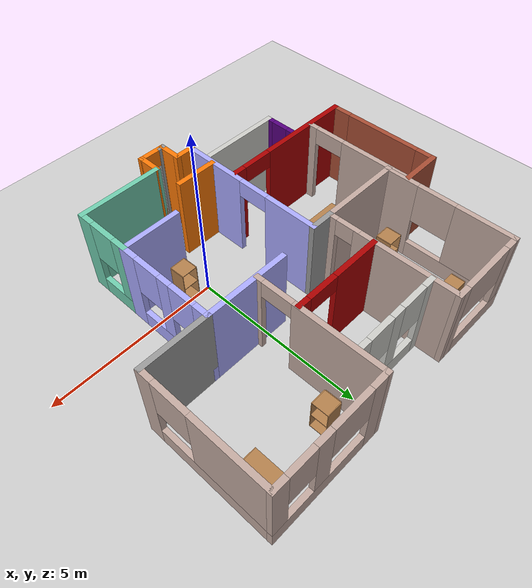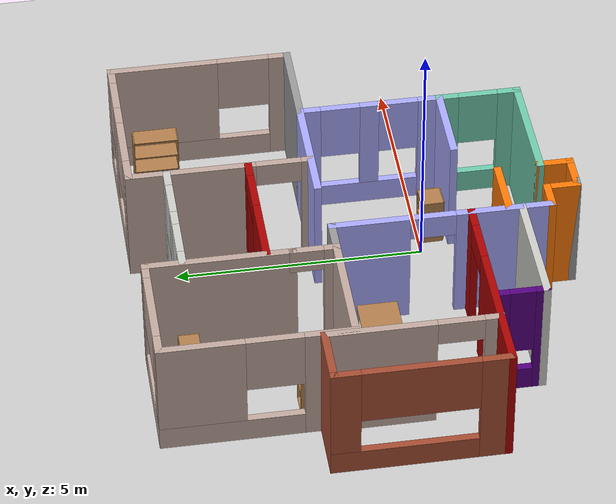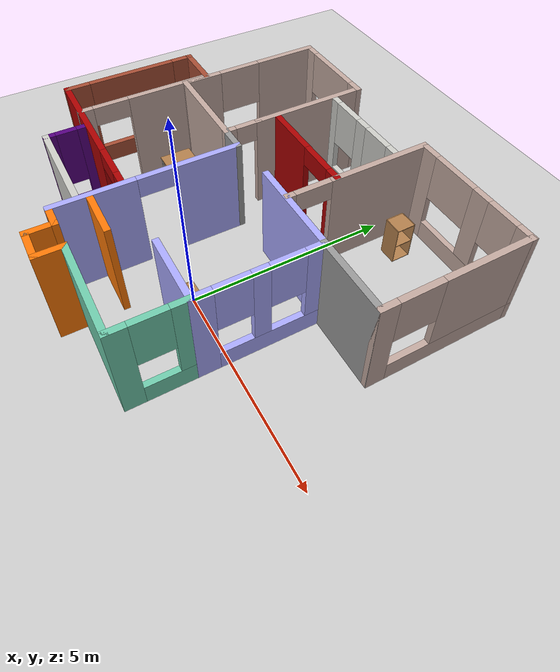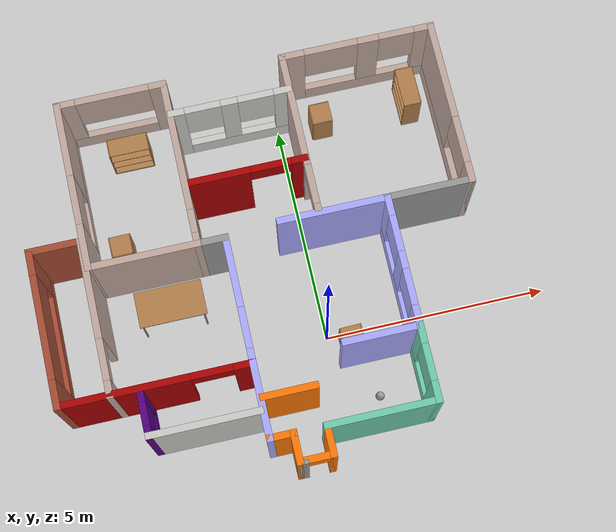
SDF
<sdf version="1.6">
 <world name="default">
  <light name="sun" type="directional">
   <pose>0 0 10 0 -0 0</pose>
   <diffuse>0.8 0.8 0.8 1</diffuse>
   <specular>0.2 0.2 0.2 1</specular>
   <attenuation>
    <range>1000</range>
    <constant>0.9</constant>
    <linear>0.01</linear>
    <quadratic>0.001</quadratic>
   </attenuation>
   <direction>-0.5 0.1 -0.9</direction>
  </light>
  <model name="ground_plane">
   <static>1</static>
   <link name="link">
    <collision name="collision">
     <geometry><plane><normal>0 0 1</normal><size>100 100</size></plane></geometry>
     <surface>
      <contact><collide_bitmask>65535</collide_bitmask></contact>
      <friction><ode><mu>100</mu><mu2>50</mu2></ode></friction>
     </surface>
    </collision>
    <visual name="visual">
     <cast_shadows>0</cast_shadows>
     <geometry><plane><normal>0 0 1</normal><size>100 100</size></plane></geometry>
     <material>
      <script><uri>file://media/materials/scripts/gazebo.material</uri><name>Gazebo/Grey</name></script>
     </material>
    </visual>
   </link>
  </model>
  <gravity>0 0 -9.8</gravity>
  <magnetic_field>6e-06 2.3e-05 -4.2e-05</magnetic_field>
  <atmosphere type="adiabatic"/>
  <physics name="default_physics" default="0" type="ode">
   <max_step_size>0.001</max_step_size>
   <real_time_factor>1</real_time_factor>
   <real_time_update_rate>1000</real_time_update_rate>
  </physics>
  <scene><ambient>0.4 0.4 0.4 1</ambient><background>0.7 0.7 0.7 1</background><shadows>1</shadows></scene>
  <spherical_coordinates>
   <surface_model>EARTH_WGS84</surface_model>
   <latitude_deg>0</latitude_deg>
   <longitude_deg>0</longitude_deg>
   <elevation>0</elevation>
   <heading_deg>0</heading_deg>
  </spherical_coordinates>
  <model name="homeGoChaseIt">
   <pose>-1.07958 1.48988 0 0 -0 0</pose>
   <link name="Wall_0">
    <pose>0.249581 -4.33988 0 0 -0 0</pose>
    <visual name="Wall_0_Visual_0">
     <pose>-0.348103 0 1.25 0 -0 0</pose>
     <geometry><box><size>0.053794 0.15 2.5</size></box></geometry>
     <material>
      <script><uri>file://media/materials/scripts/gazebo.material</uri><name>Gazebo/Grey</name></script>
      <ambient>0.996078 0.47451 0.0196078 1</ambient>
     </material>
     <meta><layer>0</layer></meta>
    </visual>
    <collision name="Wall_0_Collision_0">
     <geometry><box><size>0.053794 0.15 2.5</size></box></geometry>
     <pose>-0.348103 0 1.25 0 -0 0</pose>
    </collision>
    <visual name="Wall_0_Visual_1">
     <pose>0.326897 0 1.25 0 -0 0</pose>
     <geometry><box><size>0.096206 0.15 2.5</size></box></geometry>
     <material>
      <script><uri>file://media/materials/scripts/gazebo.material</uri><name>Gazebo/Grey</name></script>
      <ambient>0.996078 0.47451 0.0196078 1</ambient>
     </material>
     <meta><layer>0</layer></meta>
    </visual>
    <collision name="Wall_0_Collision_1">
     <geometry><box><size>0.096206 0.15 2.5</size></box></geometry>
     <pose>0.326897 0 1.25 0 -0 0</pose>
    </collision>
    <visual name="Wall_0_Visual_2">
     <pose>-0.021206 0 2.25 0 -0 0</pose>
     <geometry><box><size>0.6 0.15 0.5</size></box></geometry>
     <material>
      <script><uri>file://media/materials/scripts/gazebo.material</uri><name>Gazebo/Grey</name></script>
      <ambient>0.996078 0.47451 0.0196078 1</ambient>
     </material>
     <meta><layer>0</layer></meta>
    </visual>
    <collision name="Wall_0_Collision_2">
     <geometry><box><size>0.6 0.15 0.5</size></box></geometry>
     <pose>-0.021206 0 2.25 0 -0 0</pose>
    </collision>
   </link>
   <link name="Wall_1">
    <collision name="Wall_1_Collision">
     <geometry><box><size>0.75 0.15 2.5</size></box></geometry>
     <pose>0 0 1.25 0 -0 0</pose>
    </collision>
    <visual name="Wall_1_Visual">
     <pose>0 0 1.25 0 -0 0</pose>
     <geometry><box><size>0.75 0.15 2.5</size></box></geometry>
     <material>
      <script><uri>file://media/materials/scripts/gazebo.material</uri><name>Gazebo/Grey</name></script>
      <ambient>0.996078 0.47451 0.0196078 1</ambient>
     </material>
     <meta><layer>0</layer></meta>
    </visual>
    <pose>0.549581 -4.03988 0 0 -0 1.5708</pose>
   </link>
   <link name="Wall_12">
    <pose>-0.650419 -1.56488 0 0 -0 1.5708</pose>
    <visual name="Wall_12_Visual_0">
     <pose>-1.2585 0 1.25 0 -0 0</pose>
     <geometry><box><size>1.983 0.15 2.5</size></box></geometry>
     <material>
      <script><uri>file://media/materials/scripts/gazebo.material</uri><name>Gazebo/Grey</name></script>
      <ambient>0.666667 0.666667 1 1</ambient>
     </material>
     <meta><layer>0</layer></meta>
    </visual>
    <collision name="Wall_12_Collision_0">
     <geometry><box><size>1.983 0.15 2.5</size></box></geometry>
     <pose>-1.2585 0 1.25 0 -0 0</pose>
    </collision>
    <visual name="Wall_12_Visual_1">
     <pose>1.4415 0 1.25 0 -0 0</pose>
     <geometry><box><size>1.617 0.15 2.5</size></box></geometry>
     <material>
      <script><uri>file://media/materials/scripts/gazebo.material</uri><name>Gazebo/Grey</name></script>
      <ambient>0.666667 0.666667 1 1</ambient>
     </material>
     <meta><layer>0</layer></meta>
    </visual>
    <collision name="Wall_12_Collision_1">
     <geometry><box><size>1.617 0.15 2.5</size></box></geometry>
     <pose>1.4415 0 1.25 0 -0 0</pose>
    </collision>
    <visual name="Wall_12_Visual_2">
     <pose>0.183002 0 2.25 0 -0 0</pose>
     <geometry><box><size>0.9 0.15 0.5</size></box></geometry>
     <material>
      <script><uri>file://media/materials/scripts/gazebo.material</uri><name>Gazebo/Grey</name></script>
      <ambient>0.666667 0.666667 1 1</ambient>
     </material>
     <meta><layer>0</layer></meta>
    </visual>
    <collision name="Wall_12_Collision_2">
     <geometry><box><size>0.9 0.15 0.5</size></box></geometry>
     <pose>0.183002 0 2.25 0 -0 0</pose>
    </collision>
   </link>
   <link name="Wall_16">
    <collision name="Wall_16_Collision">
     <geometry><box><size>0.75 0.15 2.5</size></box></geometry>
     <pose>0 0 1.25 0 -0 0</pose>
    </collision>
    <visual name="Wall_16_Visual">
     <pose>0 0 1.25 0 -0 0</pose>
     <geometry><box><size>0.75 0.15 2.5</size></box></geometry>
     <material>
      <script><uri>file://media/materials/scripts/gazebo.material</uri><name>Gazebo/Grey</name></script>
      <ambient>1 1 1 1</ambient>
     </material>
     <meta><layer>0</layer></meta>
    </visual>
    <pose>-0.950419 0.610124 0 0 -0 3.14159</pose>
   </link>
   <link name="Wall_17">
    <pose>-1.25042 1.03512 0 0 -0 1.5708</pose>
    <visual name="Wall_17_Visual_0">
     <pose>-0.337999 0 1.25 0 -0 0</pose>
     <geometry><box><size>0.324002 0.15 2.5</size></box></geometry>
     <material>
      <script><uri>file://media/materials/scripts/gazebo.material</uri><name>Gazebo/Grey</name></script>
      <ambient>0.760784 0.662745 0.627451 1</ambient>
     </material>
     <meta><layer>0</layer></meta>
    </visual>
    <collision name="Wall_17_Collision_0">
     <geometry><box><size>0.324002 0.15 2.5</size></box></geometry>
     <pose>-0.337999 0 1.25 0 -0 0</pose>
    </collision>
    <visual name="Wall_17_Visual_1">
     <pose>0.162001 0 2.25 0 -0 0</pose>
     <geometry><box><size>0.675998 0.15 0.5</size></box></geometry>
     <material>
      <script><uri>file://media/materials/scripts/gazebo.material</uri><name>Gazebo/Grey</name></script>
      <ambient>0.760784 0.662745 0.627451 1</ambient>
     </material>
     <meta><layer>0</layer></meta>
    </visual>
    <collision name="Wall_17_Collision_1">
     <geometry><box><size>0.675998 0.15 0.5</size></box></geometry>
     <pose>0.162001 0 2.25 0 -0 0</pose>
    </collision>
   </link>
   <link name="Wall_2">
    <collision name="Wall_2_Collision">
     <geometry><box><size>2.5 0.15 2.5</size></box></geometry>
     <pose>0 0 1.25 0 -0 0</pose>
    </collision>
    <visual name="Wall_2_Visual">
     <pose>0 0 1.25 0 -0 0</pose>
     <geometry><box><size>2.5 0.15 2.5</size></box></geometry>
     <material>
      <script><uri>file://media/materials/scripts/gazebo.material</uri><name>Gazebo/Grey</name></script>
      <ambient>0.435294 0.796078 0.67451 1</ambient>
     </material>
     <meta><layer>0</layer></meta>
    </visual>
    <pose>1.72458 -3.73988 0 0 -0 0</pose>
   </link>
   <link name="Wall_21">
    <collision name="Wall_21_Collision">
     <geometry><box><size>3 0.15 2.5</size></box></geometry>
     <pose>0 0 1.25 0 -0 0</pose>
    </collision>
    <visual name="Wall_21_Visual">
     <pose>0 0 1.25 0 -0 0</pose>
     <geometry><box><size>3 0.15 2.5</size></box></geometry>
     <material>
      <script><uri>file://media/materials/scripts/gazebo.material</uri><name>Gazebo/Grey</name></script>
      <ambient>0.760784 0.662745 0.627451 1</ambient>
     </material>
     <meta><layer>0</layer></meta>
    </visual>
    <pose>-1.25042 2.88512 0 0 -0 1.5708</pose>
   </link>
   <link name="Wall_22">
    <pose>-2.42542 4.31012 0 0 -0 3.14159</pose>
    <visual name="Wall_22_Visual_0">
     <pose>-1.0479 0 1.25 0 -0 0</pose>
     <geometry><box><size>0.404205 0.15 2.5</size></box></geometry>
     <material>
      <script><uri>file://media/materials/scripts/gazebo.material</uri><name>Gazebo/Grey</name></script>
      <ambient>0.760784 0.662745 0.627451 1</ambient>
     </material>
     <meta><layer>0</layer></meta>
    </visual>
    <collision name="Wall_22_Collision_0">
     <geometry><box><size>0.404205 0.15 2.5</size></box></geometry>
     <pose>-1.0479 0 1.25 0 -0 0</pose>
    </collision>
    <visual name="Wall_22_Visual_1">
     <pose>0.202103 0 0.25 0 -0 0</pose>
     <geometry><box><size>2.09579 0.15 0.5</size></box></geometry>
     <material>
      <script><uri>file://media/materials/scripts/gazebo.material</uri><name>Gazebo/Grey</name></script>
      <ambient>0.760784 0.662745 0.627451 1</ambient>
     </material>
     <meta><layer>0</layer></meta>
    </visual>
    <collision name="Wall_22_Collision_1">
     <geometry><box><size>2.09579 0.15 0.5</size></box></geometry>
     <pose>0.202103 0 0.25 0 -0 0</pose>
    </collision>
    <visual name="Wall_22_Visual_2">
     <pose>1.0161 0 1.5 0 -0 0</pose>
     <geometry><box><size>0.467795 0.15 2</size></box></geometry>
     <material>
      <script><uri>file://media/materials/scripts/gazebo.material</uri><name>Gazebo/Grey</name></script>
      <ambient>0.760784 0.662745 0.627451 1</ambient>
     </material>
     <meta><layer>0</layer></meta>
    </visual>
    <collision name="Wall_22_Collision_2">
     <geometry><box><size>0.467795 0.15 2</size></box></geometry>
     <pose>1.0161 0 1.5 0 -0 0</pose>
    </collision>
    <visual name="Wall_22_Visual_3">
     <pose>-0.031795 0 1.9 0 -0 0</pose>
     <geometry><box><size>1.628 0.15 1.2</size></box></geometry>
     <material>
      <script><uri>file://media/materials/scripts/gazebo.material</uri><name>Gazebo/Grey</name></script>
      <ambient>0.760784 0.662745 0.627451 1</ambient>
     </material>
     <meta><layer>0</layer></meta>
    </visual>
    <collision name="Wall_22_Collision_3">
     <geometry><box><size>1.628 0.15 1.2</size></box></geometry>
     <pose>-0.031795 0 1.9 0 -0 0</pose>
    </collision>
   </link>
   <link name="Wall_26">
    <pose>0.079375 3.58613 0 0 -0 0</pose>
    <visual name="Wall_26_Visual_0">
     <pose>-1.1925 0 1.25 0 -0 0</pose>
     <geometry><box><size>0.365 0.15 2.5</size></box></geometry>
     <material>
      <script><uri>file://media/materials/scripts/gazebo.material</uri><name>Gazebo/CeilingTiled</name></script>
      <ambient>1 1 1 1</ambient>
     </material>
     <meta><layer>0</layer></meta>
    </visual>
    <collision name="Wall_26_Collision_0">
     <geometry><box><size>0.365 0.15 2.5</size></box></geometry>
     <pose>-1.1925 0 1.25 0 -0 0</pose>
    </collision>
    <visual name="Wall_26_Visual_1">
     <pose>0.1825 0 0.25 0 -0 0</pose>
     <geometry><box><size>2.385 0.15 0.5</size></box></geometry>
     <material>
      <script><uri>file://media/materials/scripts/gazebo.material</uri><name>Gazebo/CeilingTiled</name></script>
      <ambient>1 1 1 1</ambient>
     </material>
     <meta><layer>0</layer></meta>
    </visual>
    <collision name="Wall_26_Collision_1">
     <geometry><box><size>2.385 0.15 0.5</size></box></geometry>
     <pose>0.1825 0 0.25 0 -0 0</pose>
    </collision>
    <visual name="Wall_26_Visual_2">
     <pose>-0.0235 0 1.5 0 -0 0</pose>
     <geometry><box><size>0.373 0.15 2</size></box></geometry>
     <material>
      <script><uri>file://media/materials/scripts/gazebo.material</uri><name>Gazebo/CeilingTiled</name></script>
      <ambient>1 1 1 1</ambient>
     </material>
     <meta><layer>0</layer></meta>
    </visual>
    <collision name="Wall_26_Collision_2">
     <geometry><box><size>0.373 0.15 2</size></box></geometry>
     <pose>-0.0235 0 1.5 0 -0 0</pose>
    </collision>
    <visual name="Wall_26_Visual_3">
     <pose>1.169 0 1.5 0 -0 0</pose>
     <geometry><box><size>0.412 0.15 2</size></box></geometry>
     <material>
      <script><uri>file://media/materials/scripts/gazebo.material</uri><name>Gazebo/CeilingTiled</name></script>
      <ambient>1 1 1 1</ambient>
     </material>
     <meta><layer>0</layer></meta>
    </visual>
    <collision name="Wall_26_Collision_3">
     <geometry><box><size>0.412 0.15 2</size></box></geometry>
     <pose>1.169 0 1.5 0 -0 0</pose>
    </collision>
    <visual name="Wall_26_Visual_4">
     <pose>-0.61 0 1.9 0 -0 0</pose>
     <geometry><box><size>0.8 0.15 1.2</size></box></geometry>
     <material>
      <script><uri>file://media/materials/scripts/gazebo.material</uri><name>Gazebo/CeilingTiled</name></script>
      <ambient>1 1 1 1</ambient>
     </material>
     <meta><layer>0</layer></meta>
    </visual>
    <collision name="Wall_26_Collision_4">
     <geometry><box><size>0.8 0.15 1.2</size></box></geometry>
     <pose>-0.61 0 1.9 0 -0 0</pose>
    </collision>
    <visual name="Wall_26_Visual_5">
     <pose>0.563 0 1.9 0 -0 0</pose>
     <geometry><box><size>0.8 0.15 1.2</size></box></geometry>
     <material>
      <script><uri>file://media/materials/scripts/gazebo.material</uri><name>Gazebo/CeilingTiled</name></script>
      <ambient>1 1 1 1</ambient>
     </material>
     <meta><layer>0</layer></meta>
    </visual>
    <collision name="Wall_26_Collision_5">
     <geometry><box><size>0.8 0.15 1.2</size></box></geometry>
     <pose>0.563 0 1.9 0 -0 0</pose>
    </collision>
   </link>
   <link name="Wall_3">
    <pose>2.89958 -2.93988 0 0 -0 1.5708</pose>
    <visual name="Wall_3_Visual_0">
     <pose>-0.634749 0 1.25 0 -0 0</pose>
     <geometry><box><size>0.480502 0.15 2.5</size></box></geometry>
     <material>
      <script><uri>file://media/materials/scripts/gazebo.material</uri><name>Gazebo/Grey</name></script>
      <ambient>0.435294 0.796078 0.67451 1</ambient>
     </material>
     <meta><layer>0</layer></meta>
    </visual>
    <collision name="Wall_3_Collision_0">
     <geometry><box><size>0.480502 0.15 2.5</size></box></geometry>
     <pose>-0.634749 0 1.25 0 -0 0</pose>
    </collision>
    <visual name="Wall_3_Visual_1">
     <pose>0.240251 0 0.25 0 -0 0</pose>
     <geometry><box><size>1.2695 0.15 0.5</size></box></geometry>
     <material>
      <script><uri>file://media/materials/scripts/gazebo.material</uri><name>Gazebo/Grey</name></script>
      <ambient>0.435294 0.796078 0.67451 1</ambient>
     </material>
     <meta><layer>0</layer></meta>
    </visual>
    <collision name="Wall_3_Collision_1">
     <geometry><box><size>1.2695 0.15 0.5</size></box></geometry>
     <pose>0.240251 0 0.25 0 -0 0</pose>
    </collision>
    <visual name="Wall_3_Visual_2">
     <pose>0.640251 0 1.5 0 -0 0</pose>
     <geometry><box><size>0.469498 0.15 2</size></box></geometry>
     <material>
      <script><uri>file://media/materials/scripts/gazebo.material</uri><name>Gazebo/Grey</name></script>
      <ambient>0.435294 0.796078 0.67451 1</ambient>
     </material>
     <meta><layer>0</layer></meta>
    </visual>
    <collision name="Wall_3_Collision_2">
     <geometry><box><size>0.469498 0.15 2</size></box></geometry>
     <pose>0.640251 0 1.5 0 -0 0</pose>
    </collision>
    <visual name="Wall_3_Visual_3">
     <pose>0.005502 0 1.9 0 -0 0</pose>
     <geometry><box><size>0.8 0.15 1.2</size></box></geometry>
     <material>
      <script><uri>file://media/materials/scripts/gazebo.material</uri><name>Gazebo/Grey</name></script>
      <ambient>0.435294 0.796078 0.67451 1</ambient>
     </material>
     <meta><layer>0</layer></meta>
    </visual>
    <collision name="Wall_3_Collision_3">
     <geometry><box><size>0.8 0.15 1.2</size></box></geometry>
     <pose>0.005502 0 1.9 0 -0 0</pose>
    </collision>
   </link>
   <link name="Wall_36">
    <collision name="Wall_36_Collision">
     <geometry><box><size>0.25 0.15 2.5</size></box></geometry>
     <pose>0 0 1.25 0 -0 0</pose>
    </collision>
    <visual name="Wall_36_Visual">
     <pose>0 0 1.25 0 -0 0</pose>
     <geometry><box><size>0.25 0.15 2.5</size></box></geometry>
     <material>
      <script><uri>file://media/materials/scripts/gazebo.material</uri><name>Gazebo/Grey</name></script>
      <ambient>1 1 1 1</ambient>
     </material>
     <meta><layer>0</layer></meta>
    </visual>
    <pose>-0.100419 -4.33988 0 0 -0 3.14159</pose>
   </link>
   <link name="Wall_37">
    <collision name="Wall_37_Collision">
     <geometry><box><size>0.75 0.15 2.5</size></box></geometry>
     <pose>0 0 1.25 0 -0 0</pose>
    </collision>
    <visual name="Wall_37_Visual">
     <pose>0 0 1.25 0 -0 0</pose>
     <geometry><box><size>0.75 0.15 2.5</size></box></geometry>
     <material>
      <script><uri>file://media/materials/scripts/gazebo.material</uri><name>Gazebo/Grey</name></script>
      <ambient>0.996078 0.47451 0.0196078 1</ambient>
     </material>
     <meta><layer>0</layer></meta>
    </visual>
    <pose>-0.150419 -4.03988 0 0 -0 1.5708</pose>
   </link>
   <link name="Wall_38">
    <collision name="Wall_38_Collision">
     <geometry><box><size>0.65 0.15 2.5</size></box></geometry>
     <pose>0 0 1.25 0 -0 0</pose>
    </collision>
    <visual name="Wall_38_Visual">
     <pose>0 0 1.25 0 -0 0</pose>
     <geometry><box><size>0.65 0.15 2.5</size></box></geometry>
     <material>
      <script><uri>file://media/materials/scripts/gazebo.material</uri><name>Gazebo/Grey</name></script>
      <ambient>0.996078 0.47451 0.0196078 1</ambient>
     </material>
     <meta><layer>0</layer></meta>
    </visual>
    <pose>-0.400419 -3.73988 0 0 -0 3.14159</pose>
   </link>
   <link name="Wall_40">
    <collision name="Wall_40_Collision">
     <geometry><box><size>2.5 0.15 2.5</size></box></geometry>
     <pose>0 0 1.25 0 -0 0</pose>
    </collision>
    <visual name="Wall_40_Visual">
     <pose>0 0 1.25 0 -0 0</pose>
     <geometry><box><size>2.5 0.15 2.5</size></box></geometry>
     <material>
      <script><uri>file://media/materials/scripts/gazebo.material</uri><name>Gazebo/Grey</name></script>
      <ambient>0.760784 0.662745 0.627451 1</ambient>
     </material>
     <meta><layer>0</layer></meta>
    </visual>
    <pose>-2.42542 0.610124 0 0 -0 3.14159</pose>
   </link>
   <link name="Wall_41">
    <pose>-3.60042 2.46012 0 0 -0 1.5708</pose>
    <visual name="Wall_41_Visual_0">
     <pose>-1.40162 0 1.25 0 -0 0</pose>
     <geometry><box><size>1.04675 0.15 2.5</size></box></geometry>
     <material>
      <script><uri>file://media/materials/scripts/gazebo.material</uri><name>Gazebo/Grey</name></script>
      <ambient>0.760784 0.662745 0.627451 1</ambient>
     </material>
     <meta><layer>0</layer></meta>
    </visual>
    <collision name="Wall_41_Collision_0">
     <geometry><box><size>1.04675 0.15 2.5</size></box></geometry>
     <pose>-1.40162 0 1.25 0 -0 0</pose>
    </collision>
    <visual name="Wall_41_Visual_1">
     <pose>0.523376 0 0.25 0 -0 0</pose>
     <geometry><box><size>2.80325 0.15 0.5</size></box></geometry>
     <material>
      <script><uri>file://media/materials/scripts/gazebo.material</uri><name>Gazebo/Grey</name></script>
      <ambient>0.760784 0.662745 0.627451 1</ambient>
     </material>
     <meta><layer>0</layer></meta>
    </visual>
    <collision name="Wall_41_Collision_1">
     <geometry><box><size>2.80325 0.15 0.5</size></box></geometry>
     <pose>0.523376 0 0.25 0 -0 0</pose>
    </collision>
    <visual name="Wall_41_Visual_2">
     <pose>1.07863 0 1.5 0 -0 0</pose>
     <geometry><box><size>1.69275 0.15 2</size></box></geometry>
     <material>
      <script><uri>file://media/materials/scripts/gazebo.material</uri><name>Gazebo/Grey</name></script>
      <ambient>0.760784 0.662745 0.627451 1</ambient>
     </material>
     <meta><layer>0</layer></meta>
    </visual>
    <collision name="Wall_41_Collision_2">
     <geometry><box><size>1.69275 0.15 2</size></box></geometry>
     <pose>1.07863 0 1.5 0 -0 0</pose>
    </collision>
    <visual name="Wall_41_Visual_3">
     <pose>-0.322998 0 1.9 0 -0 0</pose>
     <geometry><box><size>1.1105 0.15 1.2</size></box></geometry>
     <material>
      <script><uri>file://media/materials/scripts/gazebo.material</uri><name>Gazebo/Grey</name></script>
      <ambient>0.760784 0.662745 0.627451 1</ambient>
     </material>
     <meta><layer>0</layer></meta>
    </visual>
    <collision name="Wall_41_Collision_3">
     <geometry><box><size>1.1105 0.15 1.2</size></box></geometry>
     <pose>-0.322998 0 1.9 0 -0 0</pose>
    </collision>
   </link>
   <link name="Wall_43">
    <collision name="Wall_43_Collision">
     <geometry><box><size>2 0.15 2.5</size></box></geometry>
     <pose>0 0 1.25 0 -0 0</pose>
    </collision>
    <visual name="Wall_43_Visual">
     <pose>0 0 1.25 0 -0 0</pose>
     <geometry><box><size>2 0.15 2.5</size></box></geometry>
     <material>
      <script><uri>file://media/materials/scripts/gazebo.material</uri><name>Gazebo/Grey</name></script>
      <ambient>1 1 1 1</ambient>
     </material>
     <meta><layer>0</layer></meta>
    </visual>
    <pose>3.82458 0.710124 0 0 -0 0</pose>
   </link>
   <link name="Wall_44">
    <pose>4.74958 2.51012 0 0 -0 1.5708</pose>
    <visual name="Wall_44_Visual_0">
     <pose>-1.64312 0 1.25 0 -0 0</pose>
     <geometry><box><size>0.463752 0.15 2.5</size></box></geometry>
     <material>
      <script><uri>file://media/materials/scripts/gazebo.material</uri><name>Gazebo/Grey</name></script>
      <ambient>0.760784 0.662745 0.627451 1</ambient>
     </material>
     <meta><layer>0</layer></meta>
    </visual>
    <collision name="Wall_44_Collision_0">
     <geometry><box><size>0.463752 0.15 2.5</size></box></geometry>
     <pose>-1.64312 0 1.25 0 -0 0</pose>
    </collision>
    <visual name="Wall_44_Visual_1">
     <pose>0.231876 0 0.25 0 -0 0</pose>
     <geometry><box><size>3.28625 0.15 0.5</size></box></geometry>
     <material>
      <script><uri>file://media/materials/scripts/gazebo.material</uri><name>Gazebo/Grey</name></script>
      <ambient>0.760784 0.662745 0.627451 1</ambient>
     </material>
     <meta><layer>0</layer></meta>
    </visual>
    <collision name="Wall_44_Collision_1">
     <geometry><box><size>3.28625 0.15 0.5</size></box></geometry>
     <pose>0.231876 0 0.25 0 -0 0</pose>
    </collision>
    <visual name="Wall_44_Visual_2">
     <pose>0.761251 0 1.5 0 -0 0</pose>
     <geometry><box><size>2.2275 0.15 2</size></box></geometry>
     <material>
      <script><uri>file://media/materials/scripts/gazebo.material</uri><name>Gazebo/Grey</name></script>
      <ambient>0.760784 0.662745 0.627451 1</ambient>
     </material>
     <meta><layer>0</layer></meta>
    </visual>
    <collision name="Wall_44_Collision_2">
     <geometry><box><size>2.2275 0.15 2</size></box></geometry>
     <pose>0.761251 0 1.5 0 -0 0</pose>
    </collision>
    <visual name="Wall_44_Visual_3">
     <pose>-0.881873 0 1.9 0 -0 0</pose>
     <geometry><box><size>1.05875 0.15 1.2</size></box></geometry>
     <material>
      <script><uri>file://media/materials/scripts/gazebo.material</uri><name>Gazebo/Grey</name></script>
      <ambient>0.760784 0.662745 0.627451 1</ambient>
     </material>
     <meta><layer>0</layer></meta>
    </visual>
    <collision name="Wall_44_Collision_3">
     <geometry><box><size>1.05875 0.15 1.2</size></box></geometry>
     <pose>-0.881873 0 1.9 0 -0 0</pose>
    </collision>
   </link>
   <link name="Wall_46">
    <pose>1.40138 2.53988 0 0 -0 1.5708</pose>
    <visual name="Wall_46_Visual_0">
     <pose>-1.752 0 1.25 0 -0 0</pose>
     <geometry><box><size>0.246 0.15 2.5</size></box></geometry>
     <material>
      <script><uri>file://media/materials/scripts/gazebo.material</uri><name>Gazebo/Grey</name></script>
      <ambient>0.760784 0.662745 0.627451 1</ambient>
     </material>
     <meta><layer>0</layer></meta>
    </visual>
    <collision name="Wall_46_Collision_0">
     <geometry><box><size>0.246 0.15 2.5</size></box></geometry>
     <pose>-1.752 0 1.25 0 -0 0</pose>
    </collision>
    <visual name="Wall_46_Visual_1">
     <pose>0.573 0 1.25 0 -0 0</pose>
     <geometry><box><size>2.604 0.15 2.5</size></box></geometry>
     <material>
      <script><uri>file://media/materials/scripts/gazebo.material</uri><name>Gazebo/Grey</name></script>
      <ambient>0.760784 0.662745 0.627451 1</ambient>
     </material>
     <meta><layer>0</layer></meta>
    </visual>
    <collision name="Wall_46_Collision_1">
     <geometry><box><size>2.604 0.15 2.5</size></box></geometry>
     <pose>0.573 0 1.25 0 -0 0</pose>
    </collision>
    <visual name="Wall_46_Visual_2">
     <pose>-1.179 0 2.25 0 -0 0</pose>
     <geometry><box><size>0.9 0.15 0.5</size></box></geometry>
     <material>
      <script><uri>file://media/materials/scripts/gazebo.material</uri><name>Gazebo/Grey</name></script>
      <ambient>0.760784 0.662745 0.627451 1</ambient>
     </material>
     <meta><layer>0</layer></meta>
    </visual>
    <collision name="Wall_46_Collision_2">
     <geometry><box><size>0.9 0.15 0.5</size></box></geometry>
     <pose>-1.179 0 2.25 0 -0 0</pose>
    </collision>
   </link>
   <link name="Wall_47">
    <pose>3.07638 4.33988 0 0 -0 0</pose>
    <visual name="Wall_47_Visual_0">
     <pose>-1.464 0 1.25 0 -0 0</pose>
     <geometry><box><size>0.572 0.15 2.5</size></box></geometry>
     <material>
      <script><uri>file://media/materials/scripts/gazebo.material</uri><name>Gazebo/Grey</name></script>
      <ambient>0.760784 0.662745 0.627451 1</ambient>
     </material>
     <meta><layer>0</layer></meta>
    </visual>
    <collision name="Wall_47_Collision_0">
     <geometry><box><size>0.572 0.15 2.5</size></box></geometry>
     <pose>-1.464 0 1.25 0 -0 0</pose>
    </collision>
    <visual name="Wall_47_Visual_1">
     <pose>0.286 0 0.25 0 -0 0</pose>
     <geometry><box><size>2.928 0.15 0.5</size></box></geometry>
     <material>
      <script><uri>file://media/materials/scripts/gazebo.material</uri><name>Gazebo/Grey</name></script>
      <ambient>0.760784 0.662745 0.627451 1</ambient>
     </material>
     <meta><layer>0</layer></meta>
    </visual>
    <collision name="Wall_47_Collision_1">
     <geometry><box><size>2.928 0.15 0.5</size></box></geometry>
     <pose>0.286 0 0.25 0 -0 0</pose>
    </collision>
    <visual name="Wall_47_Visual_2">
     <pose>0.257 0 1.5 0 -0 0</pose>
     <geometry><box><size>0.4765 0.15 2</size></box></geometry>
     <material>
      <script><uri>file://media/materials/scripts/gazebo.material</uri><name>Gazebo/Grey</name></script>
      <ambient>0.760784 0.662745 0.627451 1</ambient>
     </material>
     <meta><layer>0</layer></meta>
    </visual>
    <collision name="Wall_47_Collision_2">
     <geometry><box><size>0.4765 0.15 2</size></box></geometry>
     <pose>0.257 0 1.5 0 -0 0</pose>
    </collision>
    <visual name="Wall_47_Visual_3">
     <pose>1.52262 0 1.5 0 -0 0</pose>
     <geometry><box><size>0.45475 0.15 2</size></box></geometry>
     <material>
      <script><uri>file://media/materials/scripts/gazebo.material</uri><name>Gazebo/Grey</name></script>
      <ambient>0.760784 0.662745 0.627451 1</ambient>
     </material>
     <meta><layer>0</layer></meta>
    </visual>
    <collision name="Wall_47_Collision_3">
     <geometry><box><size>0.45475 0.15 2</size></box></geometry>
     <pose>1.52262 0 1.5 0 -0 0</pose>
    </collision>
    <visual name="Wall_47_Visual_4">
     <pose>-0.579625 0 1.9 0 -0 0</pose>
     <geometry><box><size>1.19675 0.15 1.2</size></box></geometry>
     <material>
      <script><uri>file://media/materials/scripts/gazebo.material</uri><name>Gazebo/Grey</name></script>
      <ambient>0.760784 0.662745 0.627451 1</ambient>
     </material>
     <meta><layer>0</layer></meta>
    </visual>
    <collision name="Wall_47_Collision_4">
     <geometry><box><size>1.19675 0.15 1.2</size></box></geometry>
     <pose>-0.579625 0 1.9 0 -0 0</pose>
    </collision>
    <visual name="Wall_47_Visual_5">
     <pose>0.89525 0 1.9 0 -0 0</pose>
     <geometry><box><size>0.8 0.15 1.2</size></box></geometry>
     <material>
      <script><uri>file://media/materials/scripts/gazebo.material</uri><name>Gazebo/Grey</name></script>
      <ambient>0.760784 0.662745 0.627451 1</ambient>
     </material>
     <meta><layer>0</layer></meta>
    </visual>
    <collision name="Wall_47_Collision_5">
     <geometry><box><size>0.8 0.15 1.2</size></box></geometry>
     <pose>0.89525 0 1.9 0 -0 0</pose>
    </collision>
   </link>
   <link name="Wall_49">
    <pose>-2.70138 -2.14087 0 0 -0 3.14159</pose>
    <visual name="Wall_49_Visual_0">
     <pose>-1.88125 0 1.25 0 -0 0</pose>
     <geometry><box><size>0.4875 0.15 2.5</size></box></geometry>
     <material>
      <script><uri>file://media/materials/scripts/gazebo.material</uri><name>Gazebo/Grey</name></script>
      <ambient>0.666667 0 0 1</ambient>
     </material>
     <meta><layer>0</layer></meta>
    </visual>
    <collision name="Wall_49_Collision_0">
     <geometry><box><size>0.4875 0.15 2.5</size></box></geometry>
     <pose>-1.88125 0 1.25 0 -0 0</pose>
    </collision>
    <visual name="Wall_49_Visual_1">
     <pose>0.69375 0 1.25 0 -0 0</pose>
     <geometry><box><size>2.8625 0.15 2.5</size></box></geometry>
     <material>
      <script><uri>file://media/materials/scripts/gazebo.material</uri><name>Gazebo/Grey</name></script>
      <ambient>0.666667 0 0 1</ambient>
     </material>
     <meta><layer>0</layer></meta>
    </visual>
    <collision name="Wall_49_Collision_1">
     <geometry><box><size>2.8625 0.15 2.5</size></box></geometry>
     <pose>0.69375 0 1.25 0 -0 0</pose>
    </collision>
    <visual name="Wall_49_Visual_2">
     <pose>-1.1875 0 2.25 0 -0 0</pose>
     <geometry><box><size>0.9 0.15 0.5</size></box></geometry>
     <material>
      <script><uri>file://media/materials/scripts/gazebo.material</uri><name>Gazebo/Grey</name></script>
      <ambient>0.666667 0 0 1</ambient>
     </material>
     <meta><layer>0</layer></meta>
    </visual>
    <collision name="Wall_49_Collision_2">
     <geometry><box><size>0.9 0.15 0.5</size></box></geometry>
     <pose>-1.1875 0 2.25 0 -0 0</pose>
    </collision>
   </link>
   <link name="Wall_5">
    <collision name="Wall_5_Collision">
     <geometry><box><size>1.75 0.15 2.5</size></box></geometry>
     <pose>0 0 1.25 0 -0 0</pose>
    </collision>
    <visual name="Wall_5_Visual">
     <pose>0 0 1.25 0 -0 0</pose>
     <geometry><box><size>1.75 0.15 2.5</size></box></geometry>
     <material>
      <script><uri>file://media/materials/scripts/gazebo.material</uri><name>Gazebo/Grey</name></script>
      <ambient>0.666667 0.666667 1 1</ambient>
     </material>
     <meta><layer>0</layer></meta>
    </visual>
    <pose>2.09958 -2.13988 0 0 -0 3.14159</pose>
   </link>
   <link name="Wall_50">
    <pose>-4.75138 -0.465874 0 0 -0 1.5708</pose>
    <visual name="Wall_50_Visual_0">
     <pose>-1.42519 0 1.25 0 -0 0</pose>
     <geometry><box><size>0.649625 0.15 2.5</size></box></geometry>
     <material>
      <script><uri>file://media/materials/scripts/gazebo.material</uri><name>Gazebo/Bricks</name></script>
      <ambient>0.435294 0.796078 0.67451 1</ambient>
     </material>
     <meta><layer>0</layer></meta>
    </visual>
    <collision name="Wall_50_Collision_0">
     <geometry><box><size>0.649625 0.15 2.5</size></box></geometry>
     <pose>-1.42519 0 1.25 0 -0 0</pose>
    </collision>
    <visual name="Wall_50_Visual_1">
     <pose>0.324812 0 0.25 0 -0 0</pose>
     <geometry><box><size>2.85038 0.15 0.5</size></box></geometry>
     <material>
      <script><uri>file://media/materials/scripts/gazebo.material</uri><name>Gazebo/Bricks</name></script>
      <ambient>0.435294 0.796078 0.67451 1</ambient>
     </material>
     <meta><layer>0</layer></meta>
    </visual>
    <collision name="Wall_50_Collision_1">
     <geometry><box><size>2.85038 0.15 0.5</size></box></geometry>
     <pose>0.324812 0 0.25 0 -0 0</pose>
    </collision>
    <visual name="Wall_50_Visual_2">
     <pose>1.45794 0 1.5 0 -0 0</pose>
     <geometry><box><size>0.584125 0.15 2</size></box></geometry>
     <material>
      <script><uri>file://media/materials/scripts/gazebo.material</uri><name>Gazebo/Bricks</name></script>
      <ambient>0.435294 0.796078 0.67451 1</ambient>
     </material>
     <meta><layer>0</layer></meta>
    </visual>
    <collision name="Wall_50_Collision_2">
     <geometry><box><size>0.584125 0.15 2</size></box></geometry>
     <pose>1.45794 0 1.5 0 -0 0</pose>
    </collision>
    <visual name="Wall_50_Visual_3">
     <pose>0.03275 0 1.9 0 -0 0</pose>
     <geometry><box><size>2.26625 0.15 1.2</size></box></geometry>
     <material>
      <script><uri>file://media/materials/scripts/gazebo.material</uri><name>Gazebo/Bricks</name></script>
      <ambient>0.435294 0.796078 0.67451 1</ambient>
     </material>
     <meta><layer>0</layer></meta>
    </visual>
    <collision name="Wall_50_Collision_3">
     <geometry><box><size>2.26625 0.15 1.2</size></box></geometry>
     <pose>0.03275 0 1.9 0 -0 0</pose>
    </collision>
   </link>
   <link name="Wall_51">
    <collision name="Wall_51_Collision">
     <geometry><box><size>1.25 0.15 2.5</size></box></geometry>
     <pose>0 0 1.25 0 -0 0</pose>
    </collision>
    <visual name="Wall_51_Visual">
     <pose>0 0 1.25 0 -0 0</pose>
     <geometry><box><size>1.25 0.15 2.5</size></box></geometry>
     <material>
      <script><uri>file://media/materials/scripts/gazebo.material</uri><name>Gazebo/Bricks</name></script>
      <ambient>0.435294 0.796078 0.67451 1</ambient>
     </material>
     <meta><layer>0</layer></meta>
    </visual>
    <pose>-4.20137 1.20913 0 0 -0 0</pose>
   </link>
   <link name="Wall_52">
    <pose>-3.65137 -0.465874 0 0 0 -1.5708</pose>
    <visual name="Wall_52_Visual_0">
     <pose>-0.642 0 1.25 0 -0 0</pose>
     <geometry><box><size>2.216 0.15 2.5</size></box></geometry>
     <material>
      <script><uri>file://media/materials/scripts/gazebo.material</uri><name>Gazebo/Grey</name></script>
      <ambient>0.760784 0.662745 0.627451 1</ambient>
     </material>
     <meta><layer>0</layer></meta>
    </visual>
    <collision name="Wall_52_Collision_0">
     <geometry><box><size>2.216 0.15 2.5</size></box></geometry>
     <pose>-0.642 0 1.25 0 -0 0</pose>
    </collision>
    <visual name="Wall_52_Visual_1">
     <pose>1.558 0 1.25 0 -0 0</pose>
     <geometry><box><size>0.384 0.15 2.5</size></box></geometry>
     <material>
      <script><uri>file://media/materials/scripts/gazebo.material</uri><name>Gazebo/Grey</name></script>
      <ambient>0.760784 0.662745 0.627451 1</ambient>
     </material>
     <meta><layer>0</layer></meta>
    </visual>
    <collision name="Wall_52_Collision_1">
     <geometry><box><size>0.384 0.15 2.5</size></box></geometry>
     <pose>1.558 0 1.25 0 -0 0</pose>
    </collision>
    <visual name="Wall_52_Visual_2">
     <pose>0.916 0 2.25 0 -0 0</pose>
     <geometry><box><size>0.9 0.15 0.5</size></box></geometry>
     <material>
      <script><uri>file://media/materials/scripts/gazebo.material</uri><name>Gazebo/Grey</name></script>
      <ambient>0.760784 0.662745 0.627451 1</ambient>
     </material>
     <meta><layer>0</layer></meta>
    </visual>
    <collision name="Wall_52_Collision_2">
     <geometry><box><size>0.9 0.15 0.5</size></box></geometry>
     <pose>0.916 0 2.25 0 -0 0</pose>
    </collision>
   </link>
   <link name="Wall_55">
    <pose>0.079375 1.96463 0 0 -0 0</pose>
    <visual name="Wall_55_Visual_0">
     <pose>-0.639625 0 1.25 0 -0 0</pose>
     <geometry><box><size>1.47075 0.15 2.5</size></box></geometry>
     <material>
      <script><uri>file://media/materials/scripts/gazebo.material</uri><name>Gazebo/Grey</name></script>
      <ambient>0.666667 0 0 1</ambient>
     </material>
     <meta><layer>0</layer></meta>
    </visual>
    <collision name="Wall_55_Collision_0">
     <geometry><box><size>1.47075 0.15 2.5</size></box></geometry>
     <pose>-0.639625 0 1.25 0 -0 0</pose>
    </collision>
    <visual name="Wall_55_Visual_1">
     <pose>1.18538 0 1.25 0 -0 0</pose>
     <geometry><box><size>0.37925 0.15 2.5</size></box></geometry>
     <material>
      <script><uri>file://media/materials/scripts/gazebo.material</uri><name>Gazebo/Grey</name></script>
      <ambient>0.666667 0 0 1</ambient>
     </material>
     <meta><layer>0</layer></meta>
    </visual>
    <collision name="Wall_55_Collision_1">
     <geometry><box><size>0.37925 0.15 2.5</size></box></geometry>
     <pose>1.18538 0 1.25 0 -0 0</pose>
    </collision>
    <visual name="Wall_55_Visual_2">
     <pose>0.54575 0 2.25 0 -0 0</pose>
     <geometry><box><size>0.9 0.15 0.5</size></box></geometry>
     <material>
      <script><uri>file://media/materials/scripts/gazebo.material</uri><name>Gazebo/Grey</name></script>
      <ambient>0.666667 0 0 1</ambient>
     </material>
     <meta><layer>0</layer></meta>
    </visual>
    <collision name="Wall_55_Collision_2">
     <geometry><box><size>0.9 0.15 0.5</size></box></geometry>
     <pose>0.54575 0 2.25 0 -0 0</pose>
    </collision>
   </link>
   <link name="Wall_57">
    <collision name="Wall_57_Collision">
     <geometry><box><size>2.5 0.15 2.5</size></box></geometry>
     <pose>0 0 1.25 0 -0 0</pose>
    </collision>
    <visual name="Wall_57_Visual">
     <pose>0 0 1.25 0 -0 0</pose>
     <geometry><box><size>2.5 0.15 2.5</size></box></geometry>
     <material>
      <script><uri>file://media/materials/scripts/gazebo.material</uri><name>Gazebo/CeilingTiled</name></script>
      <ambient>1 1 1 1</ambient>
     </material>
     <meta><layer>0</layer></meta>
    </visual>
    <pose>-1.86088 -3.14137 0 0 -0 3.14159</pose>
   </link>
   <link name="Wall_58">
    <pose>-3.03587 -2.71637 0 0 -0 1.5708</pose>
    <visual name="Wall_58_Visual_0">
     <pose>-0.354625 0 1.25 0 -0 0</pose>
     <geometry><box><size>0.29075 0.15 2.5</size></box></geometry>
     <material>
      <script><uri>file://media/materials/scripts/gazebo.material</uri><name>Gazebo/Grey</name></script>
      <ambient>0.333333 0 0.498039 1</ambient>
     </material>
     <meta><layer>0</layer></meta>
    </visual>
    <collision name="Wall_58_Collision_0">
     <geometry><box><size>0.29075 0.15 2.5</size></box></geometry>
     <pose>-0.354625 0 1.25 0 -0 0</pose>
    </collision>
    <visual name="Wall_58_Visual_1">
     <pose>0.145375 0 0.25 0 -0 0</pose>
     <geometry><box><size>0.70925 0.15 0.5</size></box></geometry>
     <material>
      <script><uri>file://media/materials/scripts/gazebo.material</uri><name>Gazebo/Grey</name></script>
      <ambient>0.333333 0 0.498039 1</ambient>
     </material>
     <meta><layer>0</layer></meta>
    </visual>
    <collision name="Wall_58_Collision_1">
     <geometry><box><size>0.70925 0.15 0.5</size></box></geometry>
     <pose>0.145375 0 0.25 0 -0 0</pose>
    </collision>
    <visual name="Wall_58_Visual_2">
     <pose>0.395375 0 1.5 0 -0 0</pose>
     <geometry><box><size>0.20925 0.15 2</size></box></geometry>
     <material>
      <script><uri>file://media/materials/scripts/gazebo.material</uri><name>Gazebo/Grey</name></script>
      <ambient>0.333333 0 0.498039 1</ambient>
     </material>
     <meta><layer>0</layer></meta>
    </visual>
    <collision name="Wall_58_Collision_2">
     <geometry><box><size>0.20925 0.15 2</size></box></geometry>
     <pose>0.395375 0 1.5 0 -0 0</pose>
    </collision>
    <visual name="Wall_58_Visual_3">
     <pose>0.04075 0 1.75 0 -0 0</pose>
     <geometry><box><size>0.5 0.15 1.5</size></box></geometry>
     <material>
      <script><uri>file://media/materials/scripts/gazebo.material</uri><name>Gazebo/Grey</name></script>
      <ambient>0.333333 0 0.498039 1</ambient>
     </material>
     <meta><layer>0</layer></meta>
    </visual>
    <collision name="Wall_58_Collision_3">
     <geometry><box><size>0.5 0.15 1.5</size></box></geometry>
     <pose>0.04075 0 1.75 0 -0 0</pose>
    </collision>
   </link>
   <link name="Wall_60">
    <collision name="Wall_60_Collision">
     <geometry><box><size>1.25 0.15 2.5</size></box></geometry>
     <pose>0 0 1.25 0 -0 0</pose>
    </collision>
    <visual name="Wall_60_Visual">
     <pose>0 0 1.25 0 -0 0</pose>
     <geometry><box><size>1.25 0.15 2.5</size></box></geometry>
     <material>
      <script><uri>file://media/materials/scripts/gazebo.material</uri><name>Gazebo/Grey</name></script>
      <ambient>0.996078 0.47451 0.0196078 1</ambient>
     </material>
     <meta><layer>0</layer></meta>
    </visual>
    <pose>-0.049625 -2.88262 0 0 -0 0</pose>
   </link>
   <link name="Wall_7">
    <pose>2.89958 -0.714876 0 0 -0 1.5708</pose>
    <visual name="Wall_7_Visual_0">
     <pose>-1.24037 0 1.25 0 -0 0</pose>
     <geometry><box><size>0.519252 0.15 2.5</size></box></geometry>
     <material>
      <script><uri>file://media/materials/scripts/gazebo.material</uri><name>Gazebo/Grey</name></script>
      <ambient>0.666667 0.666667 1 1</ambient>
     </material>
     <meta><layer>0</layer></meta>
    </visual>
    <collision name="Wall_7_Collision_0">
     <geometry><box><size>0.519252 0.15 2.5</size></box></geometry>
     <pose>-1.24037 0 1.25 0 -0 0</pose>
    </collision>
    <visual name="Wall_7_Visual_1">
     <pose>0.259626 0 0.25 0 -0 0</pose>
     <geometry><box><size>2.48075 0.15 0.5</size></box></geometry>
     <material>
      <script><uri>file://media/materials/scripts/gazebo.material</uri><name>Gazebo/Grey</name></script>
      <ambient>0.666667 0.666667 1 1</ambient>
     </material>
     <meta><layer>0</layer></meta>
    </visual>
    <collision name="Wall_7_Collision_1">
     <geometry><box><size>2.48075 0.15 0.5</size></box></geometry>
     <pose>0.259626 0 0.25 0 -0 0</pose>
    </collision>
    <visual name="Wall_7_Visual_2">
     <pose>0.014377 0 1.5 0 -0 0</pose>
     <geometry><box><size>0.39025 0.15 2</size></box></geometry>
     <material>
      <script><uri>file://media/materials/scripts/gazebo.material</uri><name>Gazebo/Grey</name></script>
      <ambient>0.666667 0.666667 1 1</ambient>
     </material>
     <meta><layer>0</layer></meta>
    </visual>
    <collision name="Wall_7_Collision_2">
     <geometry><box><size>0.39025 0.15 2</size></box></geometry>
     <pose>0.014377 0 1.5 0 -0 0</pose>
    </collision>
    <visual name="Wall_7_Visual_3">
     <pose>1.25475 0 1.5 0 -0 0</pose>
     <geometry><box><size>0.490498 0.15 2</size></box></geometry>
     <material>
      <script><uri>file://media/materials/scripts/gazebo.material</uri><name>Gazebo/Grey</name></script>
      <ambient>0.666667 0.666667 1 1</ambient>
     </material>
     <meta><layer>0</layer></meta>
    </visual>
    <collision name="Wall_7_Collision_3">
     <geometry><box><size>0.490498 0.15 2</size></box></geometry>
     <pose>1.25475 0 1.5 0 -0 0</pose>
    </collision>
    <visual name="Wall_7_Visual_4">
     <pose>-0.580748 0 1.9 0 -0 0</pose>
     <geometry><box><size>0.8 0.15 1.2</size></box></geometry>
     <material>
      <script><uri>file://media/materials/scripts/gazebo.material</uri><name>Gazebo/Grey</name></script>
      <ambient>0.666667 0.666667 1 1</ambient>
     </material>
     <meta><layer>0</layer></meta>
    </visual>
    <collision name="Wall_7_Collision_4">
     <geometry><box><size>0.8 0.15 1.2</size></box></geometry>
     <pose>-0.580748 0 1.9 0 -0 0</pose>
    </collision>
    <visual name="Wall_7_Visual_5">
     <pose>0.609502 0 1.9 0 -0 0</pose>
     <geometry><box><size>0.8 0.15 1.2</size></box></geometry>
     <material>
      <script><uri>file://media/materials/scripts/gazebo.material</uri><name>Gazebo/Grey</name></script>
      <ambient>0.666667 0.666667 1 1</ambient>
     </material>
     <meta><layer>0</layer></meta>
    </visual>
    <collision name="Wall_7_Collision_5">
     <geometry><box><size>0.8 0.15 1.2</size></box></geometry>
     <pose>0.609502 0 1.9 0 -0 0</pose>
    </collision>
   </link>
   <link name="Wall_8">
    <collision name="Wall_8_Collision">
     <geometry><box><size>2.5 0.15 2.5</size></box></geometry>
     <pose>0 0 1.25 0 -0 0</pose>
    </collision>
    <visual name="Wall_8_Visual">
     <pose>0 0 1.25 0 -0 0</pose>
     <geometry><box><size>2.5 0.15 2.5</size></box></geometry>
     <material>
      <script><uri>file://media/materials/scripts/gazebo.material</uri><name>Gazebo/Grey</name></script>
      <ambient>0.666667 0.666667 1 1</ambient>
     </material>
     <meta><layer>0</layer></meta>
    </visual>
    <pose>1.72458 0.710124 0 0 -0 3.14159</pose>
   </link>
   <static>1</static>
  </model>
  <model name="bookshelf">
   <static>1</static>
   <link name="link">
    <inertial><mass>1</mass></inertial>
    <collision name="back">
     <pose>0 0.005 0.6 0 -0 0</pose>
     <geometry><box><size>0.9 0.01 1.2</size></box></geometry>
    </collision>
    <visual name="visual1">
     <pose>0 0.005 0.6 0 -0 0</pose>
     <geometry><box><size>0.9 0.01 1.2</size></box></geometry>
     <material>
      <script><uri>file://media/materials/scripts/gazebo.material</uri><name>Gazebo/Wood</name></script>
     </material>
    </visual>
    <collision name="left_side">
     <pose>0.45 -0.195 0.6 0 -0 0</pose>
     <geometry><box><size>0.02 0.4 1.2</size></box></geometry>
    </collision>
    <visual name="visual2">
     <pose>0.45 -0.195 0.6 0 -0 0</pose>
     <geometry><box><size>0.02 0.4 1.2</size></box></geometry>
     <material>
      <script><uri>file://media/materials/scripts/gazebo.material</uri><name>Gazebo/Wood</name></script>
     </material>
    </visual>
    <collision name="right_side">
     <pose>-0.45 -0.195 0.6 0 -0 0</pose>
     <geometry><box><size>0.02 0.4 1.2</size></box></geometry>
    </collision>
    <visual name="visual3">
     <pose>-0.45 -0.195 0.6 0 -0 0</pose>
     <geometry><box><size>0.02 0.4 1.2</size></box></geometry>
     <material>
      <script><uri>file://media/materials/scripts/gazebo.material</uri><name>Gazebo/Wood</name></script>
     </material>
    </visual>
    <collision name="bottom">
     <pose>0 -0.195 0.03 0 -0 0</pose>
     <geometry><box><size>0.88 0.4 0.06</size></box></geometry>
    </collision>
    <visual name="visual4">
     <pose>0 -0.195 0.03 0 -0 0</pose>
     <geometry><box><size>0.88 0.4 0.06</size></box></geometry>
     <material>
      <script><uri>file://media/materials/scripts/gazebo.material</uri><name>Gazebo/Wood</name></script>
     </material>
    </visual>
    <collision name="top">
     <pose>0 -0.195 1.19 0 -0 0</pose>
     <geometry><box><size>0.88 0.4 0.02</size></box></geometry>
    </collision>
    <visual name="visual5">
     <pose>0 -0.195 1.19 0 -0 0</pose>
     <geometry><box><size>0.88 0.4 0.02</size></box></geometry>
     <material>
      <script><uri>file://media/materials/scripts/gazebo.material</uri><name>Gazebo/Wood</name></script>
     </material>
    </visual>
    <collision name="low_shelf">
     <pose>0 -0.195 0.43 0 -0 0</pose>
     <geometry><box><size>0.88 0.4 0.02</size></box></geometry>
    </collision>
    <visual name="visual6">
     <pose>0 -0.195 0.43 0 -0 0</pose>
     <geometry><box><size>0.88 0.4 0.02</size></box></geometry>
     <material>
      <script><uri>file://media/materials/scripts/gazebo.material</uri><name>Gazebo/Wood</name></script>
     </material>
    </visual>
    <collision name="high_shelf">
     <pose>0 -0.195 0.8 0 -0 0</pose>
     <geometry><box><size>0.88 0.4 0.02</size></box></geometry>
    </collision>
    <visual name="visual7">
     <pose>0 -0.195 0.8 0 -0 0</pose>
     <geometry><box><size>0.88 0.4 0.02</size></box></geometry>
     <material>
      <script><uri>file://media/materials/scripts/gazebo.material</uri><name>Gazebo/Wood</name></script>
     </material>
    </visual>
   </link>
   <pose>3.24463 5.04664 0 0 0 -1.57</pose>
  </model>
  <model name="bookshelf_0">
   <static>1</static>
   <link name="link">
    <inertial><mass>1</mass></inertial>
    <collision name="back">
     <pose>0 0.005 0.6 0 -0 0</pose>
     <geometry><box><size>0.9 0.01 1.2</size></box></geometry>
    </collision>
    <visual name="visual1">
     <pose>0 0.005 0.6 0 -0 0</pose>
     <geometry><box><size>0.9 0.01 1.2</size></box></geometry>
     <material>
      <script><uri>file://media/materials/scripts/gazebo.material</uri><name>Gazebo/Wood</name></script>
     </material>
    </visual>
    <collision name="left_side">
     <pose>0.45 -0.195 0.6 0 -0 0</pose>
     <geometry><box><size>0.02 0.4 1.2</size></box></geometry>
    </collision>
    <visual name="visual2">
     <pose>0.45 -0.195 0.6 0 -0 0</pose>
     <geometry><box><size>0.02 0.4 1.2</size></box></geometry>
     <material>
      <script><uri>file://media/materials/scripts/gazebo.material</uri><name>Gazebo/Wood</name></script>
     </material>
    </visual>
    <collision name="right_side">
     <pose>-0.45 -0.195 0.6 0 -0 0</pose>
     <geometry><box><size>0.02 0.4 1.2</size></box></geometry>
    </collision>
    <visual name="visual3">
     <pose>-0.45 -0.195 0.6 0 -0 0</pose>
     <geometry><box><size>0.02 0.4 1.2</size></box></geometry>
     <material>
      <script><uri>file://media/materials/scripts/gazebo.material</uri><name>Gazebo/Wood</name></script>
     </material>
    </visual>
    <collision name="bottom">
     <pose>0 -0.195 0.03 0 -0 0</pose>
     <geometry><box><size>0.88 0.4 0.06</size></box></geometry>
    </collision>
    <visual name="visual4">
     <pose>0 -0.195 0.03 0 -0 0</pose>
     <geometry><box><size>0.88 0.4 0.06</size></box></geometry>
     <material>
      <script><uri>file://media/materials/scripts/gazebo.material</uri><name>Gazebo/Wood</name></script>
     </material>
    </visual>
    <collision name="top">
     <pose>0 -0.195 1.19 0 -0 0</pose>
     <geometry><box><size>0.88 0.4 0.02</size></box></geometry>
    </collision>
    <visual name="visual5">
     <pose>0 -0.195 1.19 0 -0 0</pose>
     <geometry><box><size>0.88 0.4 0.02</size></box></geometry>
     <material>
      <script><uri>file://media/materials/scripts/gazebo.material</uri><name>Gazebo/Wood</name></script>
     </material>
    </visual>
    <collision name="low_shelf">
     <pose>0 -0.195 0.43 0 -0 0</pose>
     <geometry><box><size>0.88 0.4 0.02</size></box></geometry>
    </collision>
    <visual name="visual6">
     <pose>0 -0.195 0.43 0 -0 0</pose>
     <geometry><box><size>0.88 0.4 0.02</size></box></geometry>
     <material>
      <script><uri>file://media/materials/scripts/gazebo.material</uri><name>Gazebo/Wood</name></script>
     </material>
    </visual>
    <collision name="high_shelf">
     <pose>0 -0.195 0.8 0 -0 0</pose>
     <geometry><box><size>0.88 0.4 0.02</size></box></geometry>
    </collision>
    <visual name="visual7">
     <pose>0 -0.195 0.8 0 -0 0</pose>
     <geometry><box><size>0.88 0.4 0.02</size></box></geometry>
     <material>
      <script><uri>file://media/materials/scripts/gazebo.material</uri><name>Gazebo/Wood</name></script>
     </material>
    </visual>
   </link>
   <pose>-3.41593 5.27768 0 0 -0 0</pose>
  </model>
  <model name="cabinet">
   <static>1</static>
   <link name="cabinet_bottom_plate">
    <inertial>
     <pose>0 0 -1 0 -0 0</pose>
     <inertia><ixx>2.05</ixx><ixy>0</ixy><ixz>0</ixz><iyy>2.05</iyy><iyz>0</iyz><izz>2.05</izz></inertia>
     <mass>25</mass>
    </inertial>
    <collision name="cabinet_bottom_plate_geom">
     <pose>0 0 0.01 0 -0 0</pose>
     <geometry><box><size>0.45 0.45 0.02</size></box></geometry>
    </collision>
    <visual name="cabinet_bottom_plate_geom_visual">
     <pose>0 0 0.01 0 -0 0</pose>
     <geometry><box><size>0.45 0.45 0.02</size></box></geometry>
     <material>
      <script><uri>file://media/materials/scripts/gazebo.material</uri><name>Gazebo/Wood</name></script>
     </material>
    </visual>
    <collision name="cabinet_bottom_plate_geom_cabinet_back_plate">
     <pose>0.235 0 0.51 0 -0 0</pose>
     <geometry><box><size>0.02 0.45 1.02</size></box></geometry>
    </collision>
    <visual name="cabinet_bottom_plate_geom_cabinet_back_plate_visual">
     <pose>0.235 0 0.51 0 -0 0</pose>
     <geometry><box><size>0.02 0.45 1.02</size></box></geometry>
     <material>
      <script><uri>file://media/materials/scripts/gazebo.material</uri><name>Gazebo/Wood</name></script>
     </material>
    </visual>
    <collision name="cabinet_bottom_plate_geom_cabinet_left_plate">
     <pose>0 0.235 0.51 0 -0 0</pose>
     <geometry><box><size>0.45 0.02 1.02</size></box></geometry>
    </collision>
    <visual name="cabinet_bottom_plate_geom_cabinet_left_plate_visual">
     <pose>0 0.235 0.51 0 -0 0</pose>
     <geometry><box><size>0.45 0.02 1.02</size></box></geometry>
     <material>
      <script><uri>file://media/materials/scripts/gazebo.material</uri><name>Gazebo/Wood</name></script>
     </material>
    </visual>
    <collision name="cabinet_bottom_plate_geom_cabinet_middle_plate">
     <pose>0 0 0.51 0 -0 0</pose>
     <geometry><box><size>0.45 0.45 0.02</size></box></geometry>
    </collision>
    <visual name="cabinet_bottom_plate_geom_cabinet_middle_plate_visual">
     <pose>0 0 0.51 0 -0 0</pose>
     <geometry><box><size>0.45 0.45 0.02</size></box></geometry>
     <material>
      <script><uri>file://media/materials/scripts/gazebo.material</uri><name>Gazebo/Wood</name></script>
     </material>
    </visual>
    <collision name="cabinet_bottom_plate_geom_cabinet_right_plate">
     <pose>0 -0.235 0.51 0 -0 0</pose>
     <geometry><box><size>0.45 0.02 1.02</size></box></geometry>
    </collision>
    <visual name="cabinet_bottom_plate_geom_cabinet_right_plate_visual">
     <pose>0 -0.235 0.51 0 -0 0</pose>
     <geometry><box><size>0.45 0.02 1.02</size></box></geometry>
     <material>
      <script><uri>file://media/materials/scripts/gazebo.material</uri><name>Gazebo/Wood</name></script>
     </material>
    </visual>
    <collision name="cabinet_bottom_plate_geom_cabinet_top_plate">
     <pose>0 0 1.01 0 -0 0</pose>
     <geometry><box><size>0.45 0.45 0.02</size></box></geometry>
    </collision>
    <visual name="cabinet_bottom_plate_geom_cabinet_top_plate_visual">
     <pose>0 0 1.01 0 -0 0</pose>
     <geometry><box><size>0.45 0.45 0.02</size></box></geometry>
     <material>
      <script><uri>file://media/materials/scripts/gazebo.material</uri><name>Gazebo/Wood</name></script>
     </material>
    </visual>
   </link>
   <pose>-4.02112 2.87105 0 0 0 -1.56224</pose>
  </model>
  <model name="cabinet_0">
   <static>1</static>
   <link name="cabinet_bottom_plate">
    <inertial>
     <pose>0 0 -1 0 -0 0</pose>
     <inertia><ixx>2.05</ixx><ixy>0</ixy><ixz>0</ixz><iyy>2.05</iyy><iyz>0</iyz><izz>2.05</izz></inertia>
     <mass>25</mass>
    </inertial>
    <collision name="cabinet_bottom_plate_geom">
     <pose>0 0 0.01 0 -0 0</pose>
     <geometry><box><size>0.45 0.45 0.02</size></box></geometry>
    </collision>
    <visual name="cabinet_bottom_plate_geom_visual">
     <pose>0 0 0.01 0 -0 0</pose>
     <geometry><box><size>0.45 0.45 0.02</size></box></geometry>
     <material>
      <script><uri>file://media/materials/scripts/gazebo.material</uri><name>Gazebo/Wood</name></script>
     </material>
    </visual>
    <collision name="cabinet_bottom_plate_geom_cabinet_back_plate">
     <pose>0.235 0 0.51 0 -0 0</pose>
     <geometry><box><size>0.02 0.45 1.02</size></box></geometry>
    </collision>
    <visual name="cabinet_bottom_plate_geom_cabinet_back_plate_visual">
     <pose>0.235 0 0.51 0 -0 0</pose>
     <geometry><box><size>0.02 0.45 1.02</size></box></geometry>
     <material>
      <script><uri>file://media/materials/scripts/gazebo.material</uri><name>Gazebo/Wood</name></script>
     </material>
    </visual>
    <collision name="cabinet_bottom_plate_geom_cabinet_left_plate">
     <pose>0 0.235 0.51 0 -0 0</pose>
     <geometry><box><size>0.45 0.02 1.02</size></box></geometry>
    </collision>
    <visual name="cabinet_bottom_plate_geom_cabinet_left_plate_visual">
     <pose>0 0.235 0.51 0 -0 0</pose>
     <geometry><box><size>0.45 0.02 1.02</size></box></geometry>
     <material>
      <script><uri>file://media/materials/scripts/gazebo.material</uri><name>Gazebo/Wood</name></script>
     </material>
    </visual>
    <collision name="cabinet_bottom_plate_geom_cabinet_middle_plate">
     <pose>0 0 0.51 0 -0 0</pose>
     <geometry><box><size>0.45 0.45 0.02</size></box></geometry>
    </collision>
    <visual name="cabinet_bottom_plate_geom_cabinet_middle_plate_visual">
     <pose>0 0 0.51 0 -0 0</pose>
     <geometry><box><size>0.45 0.45 0.02</size></box></geometry>
     <material>
      <script><uri>file://media/materials/scripts/gazebo.material</uri><name>Gazebo/Wood</name></script>
     </material>
    </visual>
    <collision name="cabinet_bottom_plate_geom_cabinet_right_plate">
     <pose>0 -0.235 0.51 0 -0 0</pose>
     <geometry><box><size>0.45 0.02 1.02</size></box></geometry>
    </collision>
    <visual name="cabinet_bottom_plate_geom_cabinet_right_plate_visual">
     <pose>0 -0.235 0.51 0 -0 0</pose>
     <geometry><box><size>0.45 0.02 1.02</size></box></geometry>
     <material>
      <script><uri>file://media/materials/scripts/gazebo.material</uri><name>Gazebo/Wood</name></script>
     </material>
    </visual>
    <collision name="cabinet_bottom_plate_geom_cabinet_top_plate">
     <pose>0 0 1.01 0 -0 0</pose>
     <geometry><box><size>0.45 0.45 0.02</size></box></geometry>
    </collision>
    <visual name="cabinet_bottom_plate_geom_cabinet_top_plate_visual">
     <pose>0 0 1.01 0 -0 0</pose>
     <geometry><box><size>0.45 0.45 0.02</size></box></geometry>
     <material>
      <script><uri>file://media/materials/scripts/gazebo.material</uri><name>Gazebo/Wood</name></script>
     </material>
    </visual>
   </link>
   <pose>0.991731 4.92313 0 0 0 -3.13188</pose>
  </model>
  <model name="cabinet_1">
   <static>1</static>
   <link name="cabinet_bottom_plate">
    <inertial>
     <pose>0 0 -1 0 -0 0</pose>
     <inertia><ixx>2.05</ixx><ixy>0</ixy><ixz>0</ixz><iyy>2.05</iyy><iyz>0</iyz><izz>2.05</izz></inertia>
     <mass>25</mass>
    </inertial>
    <collision name="cabinet_bottom_plate_geom">
     <pose>0 0 0.01 0 -0 0</pose>
     <geometry><box><size>0.45 0.45 0.02</size></box></geometry>
    </collision>
    <visual name="cabinet_bottom_plate_geom_visual">
     <pose>0 0 0.01 0 -0 0</pose>
     <geometry><box><size>0.45 0.45 0.02</size></box></geometry>
     <material>
      <script><uri>file://media/materials/scripts/gazebo.material</uri><name>Gazebo/Wood</name></script>
     </material>
    </visual>
    <collision name="cabinet_bottom_plate_geom_cabinet_back_plate">
     <pose>0.235 0 0.51 0 -0 0</pose>
     <geometry><box><size>0.02 0.45 1.02</size></box></geometry>
    </collision>
    <visual name="cabinet_bottom_plate_geom_cabinet_back_plate_visual">
     <pose>0.235 0 0.51 0 -0 0</pose>
     <geometry><box><size>0.02 0.45 1.02</size></box></geometry>
     <material>
      <script><uri>file://media/materials/scripts/gazebo.material</uri><name>Gazebo/Wood</name></script>
     </material>
    </visual>
    <collision name="cabinet_bottom_plate_geom_cabinet_left_plate">
     <pose>0 0.235 0.51 0 -0 0</pose>
     <geometry><box><size>0.45 0.02 1.02</size></box></geometry>
    </collision>
    <visual name="cabinet_bottom_plate_geom_cabinet_left_plate_visual">
     <pose>0 0.235 0.51 0 -0 0</pose>
     <geometry><box><size>0.45 0.02 1.02</size></box></geometry>
     <material>
      <script><uri>file://media/materials/scripts/gazebo.material</uri><name>Gazebo/Wood</name></script>
     </material>
    </visual>
    <collision name="cabinet_bottom_plate_geom_cabinet_middle_plate">
     <pose>0 0 0.51 0 -0 0</pose>
     <geometry><box><size>0.45 0.45 0.02</size></box></geometry>
    </collision>
    <visual name="cabinet_bottom_plate_geom_cabinet_middle_plate_visual">
     <pose>0 0 0.51 0 -0 0</pose>
     <geometry><box><size>0.45 0.45 0.02</size></box></geometry>
     <material>
      <script><uri>file://media/materials/scripts/gazebo.material</uri><name>Gazebo/Wood</name></script>
     </material>
    </visual>
    <collision name="cabinet_bottom_plate_geom_cabinet_right_plate">
     <pose>0 -0.235 0.51 0 -0 0</pose>
     <geometry><box><size>0.45 0.02 1.02</size></box></geometry>
    </collision>
    <visual name="cabinet_bottom_plate_geom_cabinet_right_plate_visual">
     <pose>0 -0.235 0.51 0 -0 0</pose>
     <geometry><box><size>0.45 0.02 1.02</size></box></geometry>
     <material>
      <script><uri>file://media/materials/scripts/gazebo.material</uri><name>Gazebo/Wood</name></script>
     </material>
    </visual>
    <collision name="cabinet_bottom_plate_geom_cabinet_top_plate">
     <pose>0 0 1.01 0 -0 0</pose>
     <geometry><box><size>0.45 0.45 0.02</size></box></geometry>
    </collision>
    <visual name="cabinet_bottom_plate_geom_cabinet_top_plate_visual">
     <pose>0 0 1.01 0 -0 0</pose>
     <geometry><box><size>0.45 0.45 0.02</size></box></geometry>
     <material>
      <script><uri>file://media/materials/scripts/gazebo.material</uri><name>Gazebo/Wood</name></script>
     </material>
    </visual>
   </link>
   <pose>0.508883 -0.262793 0 0 0 -1.54337</pose>
  </model>
  <model name="table">
   <static>1</static>
   <link name="link">
    <collision name="surface">
     <pose>0 0 1 0 -0 0</pose>
     <geometry><box><size>1.5 0.8 0.03</size></box></geometry>
     <surface><friction><ode><mu>0.6</mu><mu2>0.6</mu2></ode></friction></surface>
    </collision>
    <visual name="visual1">
     <pose>0 0 1 0 -0 0</pose>
     <geometry><box><size>1.5 0.8 0.03</size></box></geometry>
     <material>
      <script><uri>file://media/materials/scripts/gazebo.material</uri><name>Gazebo/Wood</name></script>
     </material>
    </visual>
    <collision name="front_left_leg">
     <pose>0.68 0.38 0.5 0 -0 0</pose>
     <geometry><cylinder><radius>0.02</radius><length>1</length></cylinder></geometry>
    </collision>
    <visual name="front_left_leg">
     <pose>0.68 0.38 0.5 0 -0 0</pose>
     <geometry><cylinder><radius>0.02</radius><length>1</length></cylinder></geometry>
     <material>
      <script><uri>file://media/materials/scripts/gazebo.material</uri><name>Gazebo/Grey</name></script>
     </material>
    </visual>
    <collision name="front_right_leg">
     <pose>0.68 -0.38 0.5 0 -0 0</pose>
     <geometry><cylinder><radius>0.02</radius><length>1</length></cylinder></geometry>
    </collision>
    <visual name="front_right_leg">
     <pose>0.68 -0.38 0.5 0 -0 0</pose>
     <geometry><cylinder><radius>0.02</radius><length>1</length></cylinder></geometry>
     <material>
      <script><uri>file://media/materials/scripts/gazebo.material</uri><name>Gazebo/Grey</name></script>
     </material>
    </visual>
    <collision name="back_right_leg">
     <pose>-0.68 -0.38 0.5 0 -0 0</pose>
     <geometry><cylinder><radius>0.02</radius><length>1</length></cylinder></geometry>
    </collision>
    <visual name="back_right_leg">
     <pose>-0.68 -0.38 0.5 0 -0 0</pose>
     <geometry><cylinder><radius>0.02</radius><length>1</length></cylinder></geometry>
     <material>
      <script><uri>file://media/materials/scripts/gazebo.material</uri><name>Gazebo/Grey</name></script>
     </material>
    </visual>
    <collision name="back_left_leg">
     <pose>-0.68 0.38 0.5 0 -0 0</pose>
     <geometry><cylinder><radius>0.02</radius><length>1</length></cylinder></geometry>
    </collision>
    <visual name="back_left_leg">
     <pose>-0.68 0.38 0.5 0 -0 0</pose>
     <geometry><cylinder><radius>0.02</radius><length>1</length></cylinder></geometry>
     <material>
      <script><uri>file://media/materials/scripts/gazebo.material</uri><name>Gazebo/Grey</name></script>
     </material>
    </visual>
   </link>
   <pose>-3.21299 1.32754 0 0 -0 0</pose>
  </model>
  <model name="my_ball">
   <link name="link_0">
    <inertial>
     <mass>1</mass>
     <inertia><ixx>0.1</ixx><ixy>0</ixy><ixz>0</ixz><iyy>0.1</iyy><iyz>0</iyz><izz>0.1</izz></inertia>
    </inertial>
    <visual name="visual">
     <geometry><sphere><radius>0.1</radius></sphere></geometry>
     <material>
      <lighting>1</lighting>
      <script><uri>file://media/materials/scripts/gazebo.material</uri><name>Gazebo/Grey</name></script>
      <shader type="pixel"><normal_map>__default__</normal_map></shader>
      <ambient>1 1 1 1</ambient>
      <diffuse>1 1 1 1</diffuse>
      <specular>1 1 1 1</specular>
      <emissive>1 1 1 1</emissive>
     </material>
    </visual>
    <collision name="collision">
     <geometry><sphere><radius>0.1</radius></sphere></geometry>
     <surface>
      <friction>
       <ode><mu>1</mu><mu2>1</mu2><fdir1>0 0 0</fdir1><slip1>0</slip1><slip2>0</slip2></ode>
       <torsional>
        <coefficient>1</coefficient>
        <patch_radius>0</patch_radius>
        <surface_radius>0</surface_radius>
        <use_patch_radius>1</use_patch_radius>
        <ode><slip>0</slip></ode>
       </torsional>
      </friction>
      <bounce><restitution_coefficient>0</restitution_coefficient><threshold>1e+06</threshold></bounce>
      <contact>
       <collide_without_contact>0</collide_without_contact>
       <collide_without_contact_bitmask>1</collide_without_contact_bitmask>
       <collide_bitmask>1</collide_bitmask>
       <ode>
        <soft_cfm>0</soft_cfm>
        <soft_erp>0.2</soft_erp>
        <kp>1e+13</kp>
        <kd>1</kd>
        <max_vel>0.01</max_vel>
        <min_depth>0</min_depth>
       </ode>
       <bullet>
        <split_impulse>1</split_impulse>
        <split_impulse_penetration_threshold>-0.01</split_impulse_penetration_threshold>
        <soft_cfm>0</soft_cfm>
        <soft_erp>0.2</soft_erp>
        <kp>1e+13</kp>
        <kd>1</kd>
       </bullet>
      </contact>
     </surface>
    </collision>
   </link>
   <static>0</static>
   <pose>0.858206 -1.54003 0.1 0 -0 0</pose>
  </model>
 </world>
</sdf>
